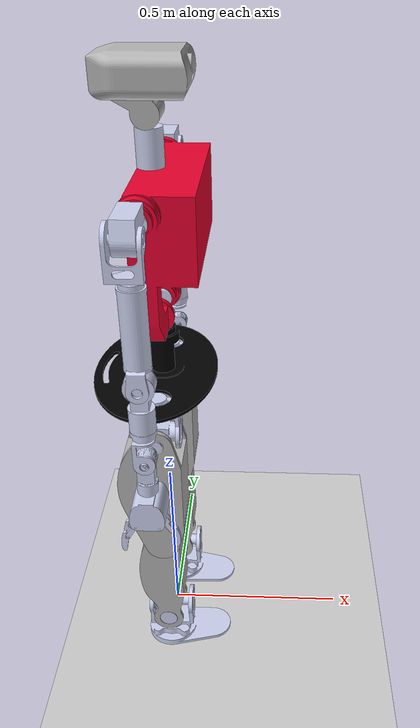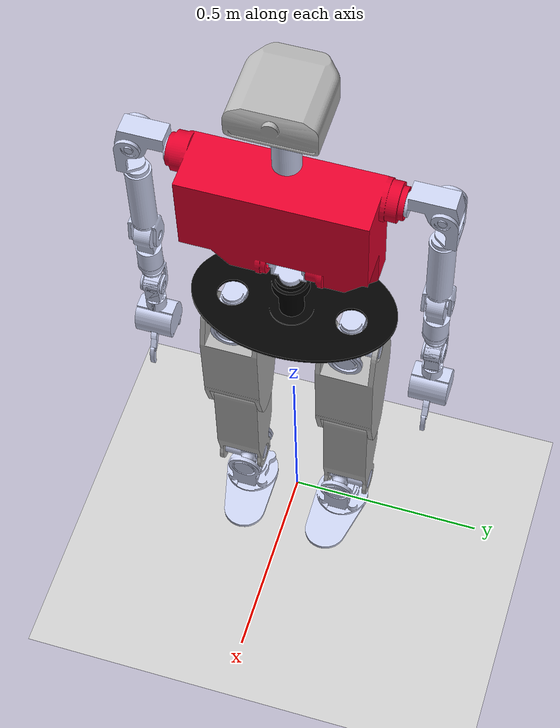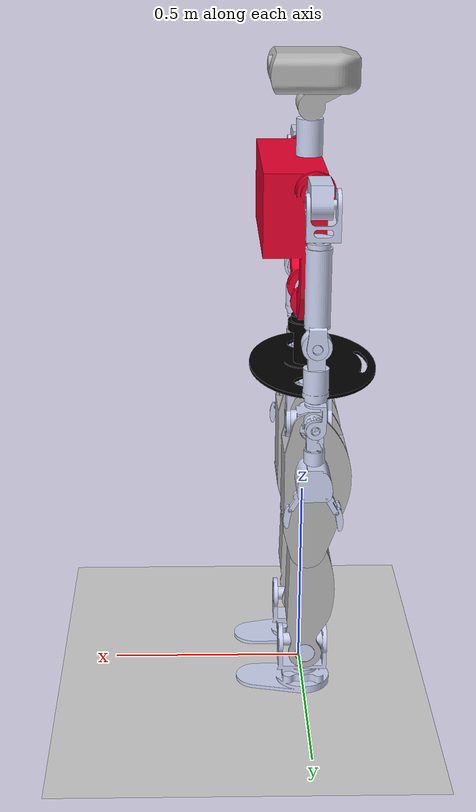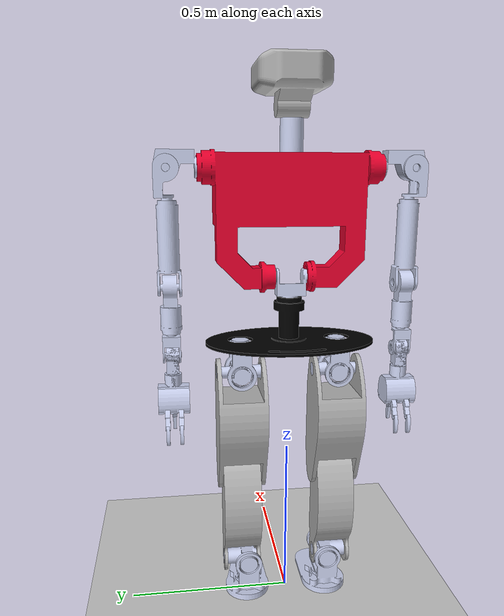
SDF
<?xml version="1.0"?>
<sdf version="1.7">
  <world name="default">

    <include>
      <uri>https://fuel.gazebosim.org/1.0/OpenRobotics/models/Sun</uri>
    </include>

    <include>
      <uri>https://fuel.gazebosim.org/1.0/OpenRobotics/models/Ground Plane</uri>
    </include>

    <include>
      <uri>model://teo_lacqueyFetch</uri>
    </include>

  </world>
</sdf>

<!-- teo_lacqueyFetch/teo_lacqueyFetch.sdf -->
<sdf version="1.7">
  <model name="TEO_lacqueyFetch">

    <include merge="true">
      <uri>model://teo</uri>
    </include>

    <include merge="true">
      <pose>0 -0.34692 0.8122 0 -0 0</pose>
      <uri>model://teo_lacqueyFetch/parts/rightLacqueyFetch.sdf</uri>
    </include>

    <joint name="RightWrist" type="fixed">
      <parent>RightSensorPlate_link</parent>
      <child>RightWrist_link</child>
    </joint>

    <include merge="true">
      <pose>0 0.34692 0.8122 0 -0 0</pose>
      <uri>model://teo_lacqueyFetch/parts/leftLacqueyFetch.sdf</uri>
    </include>

    <joint name="LeftWrist" type="fixed">
      <parent>LeftSensorPlate_link</parent>
      <child>LeftWrist_link</child>
    </joint>

    <plugin name="gzyarp::RobotInterface" filename="gz-sim-yarp-robotinterface-system">
      <yarpRobotInterfaceConfigurationFile>model://teo_lacqueyFetch/conf/teo_lacqueyFetch_nws_yarp.xml</yarpRobotInterfaceConfigurationFile>
    </plugin>

  </model>
</sdf>

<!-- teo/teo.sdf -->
<sdf version="1.7">
  <model name="TEO">

    <pose>0 0 0.845 0 -0 0</pose>

    <!-- ROOT -->

    <include merge="true">
      <uri>model://teo/parts/root.sdf</uri>
    </include>

    <joint name="AxialTrunk_adapter" type="fixed">
      <parent>RootWaist_links</parent>
      <child>AxialTrunk_link_adapter</child>
    </joint>

    <!-- TRUNK -->

    <include merge="true">
      <pose>0 0 0.1932 0 -0 0</pose>
      <uri>model://teo/parts/trunk.sdf</uri>
    </include>

    <!-- HEAD -->

    <include merge="true">
      <pose>0 0 0.6282 0 -0 0</pose>
      <uri>model://teo/parts/head.sdf</uri>
    </include>

    <joint name="AxialNeck_adapter" type="fixed">
      <parent>FrontalTrunk_link</parent>
      <child>AxialNeck_link_adapter</child>
    </joint>

    <!-- RIGHT ARM -->

    <include merge="true">
      <pose>0 -0.26292 0.4982 0 -0 0</pose>
      <uri>model://teo/parts/rightArm.sdf</uri>
    </include>

    <joint name="FrontalRightShoulder_adapter" type="fixed">
      <parent>FrontalTrunk_link</parent>
      <child>FrontalRightShoulder_link_adapter</child>
    </joint>

    <!-- LEFT ARM -->

    <include merge="true">
      <pose>0 0.26292 0.4982 0 -0 0</pose>
      <uri>model://teo/parts/leftArm.sdf</uri>
    </include>

    <joint name="FrontalLeftShoulder_adapter" type="fixed">
      <parent>FrontalTrunk_link</parent>
      <child>FrontalLeftShoulder_link_adapter</child>
    </joint>

    <!-- RIGHT LEG -->

    <include merge="true">
      <pose>0 -0.146 0 0 -0 0</pose>
      <uri>model://teo/parts/rightLeg.sdf</uri>
    </include>

    <joint name="AxialRightHip_adapter" type="fixed">
      <parent>RootWaist_links</parent>
      <child>AxialRightHip_link_adapter</child>
    </joint>

    <!-- LEFT LEG -->

    <include merge="true">
      <pose>0 0.146 0 0 -0 0</pose>
      <uri>model://teo/parts/leftLeg.sdf</uri>
    </include>

    <joint name="AxialLeftHip_adapter" type="fixed">
      <parent>RootWaist_links</parent>
      <child>AxialLeftHip_link_adapter</child>
    </joint>

    <plugin name="gz::sim::systems::SceneBroadcaster" filename="gz-sim-scene-broadcaster-system" />
    <plugin name="gz::sim::systems::Sensors" filename="gz-sim-sensors-system" />
    <plugin name="gz::sim::systems::ForceTorque" filename="gz-sim-forcetorque-system" />
    <plugin name="gz::sim::systems::Imu" filename="gz-sim-imu-system" />

    <plugin name="gzyarp::RobotInterface" filename="gz-sim-yarp-robotinterface-system">
      <yarpRobotInterfaceConfigurationFile>model://teo/conf/teo_nws_yarp.xml</yarpRobotInterfaceConfigurationFile>
    </plugin>

    <plugin name="gzyarp::RobotInterface" filename="gz-sim-yarp-robotinterface-system">
      <yarpRobotInterfaceConfigurationFile>model://teo/conf/teo_nws_ros2.xml</yarpRobotInterfaceConfigurationFile>
    </plugin>

  </model>
</sdf>

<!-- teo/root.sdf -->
<sdf version='1.7'>
<model name='TEO_root'>
  <link name='RootWaist_links'>
    <pose>0 0 0 0 -0 0</pose>
    <inertial>
      <pose>-0.010985 -0.000323 0.033148 0 -0 0</pose>
      <mass>2.5</mass>
      <inertia>
        <ixx>0.038530767</ixx>
        <ixy>-0.000000135</ixy>
        <ixz>0.000238121</ixz>
        <iyy>0.017354343</iyy>
        <iyz>-4.8e-10</iyz>
        <izz>0.053231634</izz>
      </inertia>
    </inertial>
    <visual name='RootWaist_links_visual'>
      <geometry>
        <mesh>
          <uri>model://teo/meshes/visual/RootWaist_links.dae</uri>
        </mesh>
      </geometry>
      <material>
        <ambient>0 0 0 1</ambient>
        <diffuse>0 0 0 1</diffuse>
        <specular>0 0 0 1</specular>
      </material>
    </visual>
    <collision name='RootWaist_links_collision'>
      <geometry>
        <mesh>
          <uri>model://teo/meshes/collision/RootWaist_links.stl</uri>
        </mesh>
      </geometry>
    </collision>
  </link>
</model>
</sdf>

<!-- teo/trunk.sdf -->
<sdf version="1.7">
  <model name="TEO">

    <link name="AxialTrunk_link_adapter"/>

    <link name="AxialTrunk_link">
      <pose>0 0 0 0 -0 0</pose>
      <inertial>
        <pose>-0.002235 -0.000979 -0.018814 0 -0 0</pose>
        <mass>1</mass>
        <inertia>
          <ixx>0.001977587</ixx>
          <ixy>0.00000206</ixy>
          <ixz>0.0000297</ixz>
          <iyy>0.000899729</iyy>
          <iyz>-0.00000307</iyz>
          <izz>0.001471749</izz>
        </inertia>
      </inertial>
      <visual name="AxialTrunk_visual">
        <geometry>
          <mesh>
            <uri>model://teo/meshes/visual/AxialWaist.dae</uri>
          </mesh>
        </geometry>
        <material>
          <ambient>0.792157 0.819608 0.933333 1</ambient>
          <diffuse>0.792157 0.819608 0.933333 1</diffuse>
          <specular>0.633726 0.655686 0.746667 1</specular>
        </material>
      </visual>
      <collision name="AxialTrunk_collision">
        <geometry>
          <mesh>
            <uri>model://teo/meshes/collision/AxialWaist.stl</uri>
          </mesh>
        </geometry>
      </collision>
    </link>

    <joint name="AxialTrunk" type="revolute">
      <parent>AxialTrunk_link_adapter</parent>
      <child>AxialTrunk_link</child>
      <axis>
        <xyz>0 0 1</xyz>
        <limit>
          <lower>-1.03</lower>
          <upper>0.81</upper>
        </limit>
        <dynamics>
          <damping>0.001</damping>
          <friction>0.7</friction>
        </dynamics>
      </axis>
    </joint>

    <link name="FrontalTrunk_link">
      <pose>0 0 0 0 -0 0</pose>
      <inertial>
        <pose>0.032985 -0.007876 0.220667 0 -0 0</pose>
        <mass>14.23545</mass>
        <inertia>
          <ixx>0.33566514</ixx>
          <ixy>0.000162127</ixy>
          <ixz>0.011858221</ixz>
          <iyy>0.126531585</iyy>
          <iyz>0.000914091</iyz>
          <izz>0.263359225</izz>
        </inertia>
      </inertial>
      <visual name="FrontalTrunk_visual">
        <geometry>
          <mesh>
            <uri>model://teo/meshes/visual/RootWaist.dae</uri>
          </mesh>
        </geometry>
        <material>
          <ambient>0.905882 0 0.172549 1</ambient>
          <diffuse>0.905882 0 0.172549 1</diffuse>
          <specular>0.452941 0 0.086275 1</specular>
        </material>
      </visual>
      <collision name="FrontalTrunk_collision">
        <geometry>
          <mesh>
            <uri>model://teo/meshes/collision/RootWaist.stl</uri>
          </mesh>
        </geometry>
      </collision>
      <sensor name="waist_imu" type="imu">
        <pose>0 0 0.05 0 3.14159 0</pose>
        <always_on>true</always_on>
        <update_rate>200</update_rate>
      </sensor>
    </link>

    <joint name="FrontalTrunk" type="revolute">
      <parent>AxialTrunk_link</parent>
      <child>FrontalTrunk_link</child>
      <axis>
        <xyz>0 1 0</xyz>
        <limit>
          <lower>-0.18</lower>
          <upper>1.58</upper>
        </limit>
        <dynamics>
          <damping>0.001</damping>
          <friction>0.7</friction>
        </dynamics>
      </axis>
    </joint>

    <plugin name="gzyarp::ControlBoard" filename="gz-sim-yarp-controlboard-system">
      <yarpConfigurationFile>model://teo/conf/gazebo_teo_trunk.ini</yarpConfigurationFile>
    </plugin>

    <plugin name="gzyarp::Imu" filename="gz-sim-yarp-imu-system">
      <yarpConfigurationFile>model://teo/conf/gazebo_teo_imu.ini</yarpConfigurationFile>
    </plugin>

  </model>
</sdf>

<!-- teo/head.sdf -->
<sdf version="1.7">
  <model name="TEO_head">

    <link name="AxialNeck_link_adapter"/>

    <link name="AxialNeck_link">
      <pose>0 0 0 0 -0 0</pose>
      <inertial>
        <pose>0.000302 0.000193 -0.0452 0 -0 0</pose>
        <mass>1</mass>
        <inertia>
          <ixx>0.000939063</ixx>
          <ixy>0</ixy>
          <ixz>0</ixz>
          <iyy>0.000939063</iyy>
          <iyz>0</iyz>
          <izz>0.000528125</izz>
        </inertia>
      </inertial>
      <visual name="AxialNeck_visual">
        <geometry>
          <mesh>
            <uri>model://teo/meshes/visual/AxialNeck.dae</uri>
          </mesh>
        </geometry>
        <material>
          <ambient>0.792157 0.819608 0.933333 1</ambient>
          <diffuse>0.792157 0.819608 0.933333 1</diffuse>
          <specular>0.633726 0.65568602 0.74666703 1</specular>
        </material>
      </visual>
      <collision name="AxialNeck_collision">
        <geometry>
          <mesh>
            <uri>model://teo/meshes/collision/AxialNeck.stl</uri>
          </mesh>
        </geometry>
      </collision>
    </link>

    <joint name="AxialNeck" type="revolute">
      <parent>AxialNeck_link_adapter</parent>
      <child>AxialNeck_link</child>
      <axis>
        <xyz>0 0 1</xyz>
        <limit>
          <lower>-1.22</lower>
          <upper>1.22</upper>
        </limit>
        <dynamics>
          <damping>0.001</damping>
          <friction>0.7</friction>
        </dynamics>
      </axis>
    </joint>

    <link name="FrontalNeck_link">
      <pose>0 0 0.0325 0 -0 0</pose>
      <inertial>
        <pose>-0.002729 -0.000086 0.067027 0 -0 0</pose>
        <mass>2</mass>
        <inertia>
          <ixx>0.007599322</ixx>
          <ixy>5.83e-09</ixy>
          <ixz>0.0000658</ixz>
          <iyy>0.008325273</iyy>
          <iyz>-7.43e-09</iyz>
          <izz>0.011403464</izz>
        </inertia>
      </inertial>
      <visual name="FrontalNeck_visual">
        <geometry>
          <mesh>
            <uri>model://teo/meshes/visual/FrontalNeck.dae</uri>
          </mesh>
        </geometry>
        <material>
          <ambient>1 1 1 1</ambient>
          <diffuse>0.7 0.7 0.7 1</diffuse>
          <specular>0.2 0.2 0.2 1</specular>
        </material>
      </visual>
      <collision name="FrontalNeck_collision">
        <geometry>
          <mesh>
            <uri>model://teo/meshes/collision/FrontalNeck.stl</uri>
          </mesh>
        </geometry>
      </collision>
      <sensor name="xtion_rgbd" type="rgbd_camera">
        <pose>0 0 0 0 -0 0</pose>
        <camera>
          <horizontal_fov>1.01</horizontal_fov>
          <image>
            <width>640</width>
            <height>480</height>
          </image>
          <clip>
            <near>0.2</near>
            <far>3.5</far>
          </clip>
          <lens>
            <intrinsics>
              <fx>525</fx>
              <fy>525</fy>
              <cx>319.5</cx>
              <cy>239.5</cy>
            </intrinsics>
          </lens>
        </camera>
        <always_on>1</always_on>
        <update_rate>30</update_rate>
        <visualize>1</visualize>
      </sensor>
    </link>

    <joint name="FrontalNeck" type="revolute">
      <parent>AxialNeck_link</parent>
      <child>FrontalNeck_link</child>
      <axis>
        <xyz>0 1 0</xyz>
        <limit>
          <lower>-0.51</lower>
          <upper>0.15</upper>
        </limit>
        <dynamics>
          <damping>0.001</damping>
          <friction>0.7</friction>
        </dynamics>
      </axis>
    </joint>

    <plugin name="gzyarp::ControlBoard" filename="gz-sim-yarp-controlboard-system">
      <yarpConfigurationFile>model://teo/conf/gazebo_teo_head.ini</yarpConfigurationFile>
    </plugin>

    <plugin name="gzyarp::DepthCamera" filename="gz-sim-yarp-depthcamera-system">
      <yarpConfigurationFile>model://teo/conf/gazebo_teo_rgbd.ini</yarpConfigurationFile>
    </plugin>

  </model>
</sdf>

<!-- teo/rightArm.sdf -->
<sdf version="1.7">
  <model name="TEO_rightArm">

    <link name="FrontalRightShoulder_link_adapter"/>

    <link name="FrontalRightShoulder_link">
      <pose>0 0 0 0 -0 0</pose>
      <inertial>
        <pose>-0.002267 -0.056164 0.008456 0 -0 0</pose>
        <mass>2</mass>
        <inertia>
          <ixx>0.004226791</ixx>
          <ixy>0.0000844</ixy>
          <ixz>-0.0000117</ixz>
          <iyy>0.002127281</iyy>
          <iyz>-0.000280493</iyz>
          <izz>0.004093161</izz>
        </inertia>
      </inertial>
      <visual name="FrontalRightShoulder_visual">
        <geometry>
          <mesh>
            <uri>model://teo/meshes/visual/FrontalRightShoulder.dae</uri>
          </mesh>
        </geometry>
        <material>
          <ambient>0.792157 0.819608 0.933333 1</ambient>
          <diffuse>0.792157 0.819608 0.933333 1</diffuse>
          <specular>0.633726 0.655686 0.746667 1</specular>
        </material>
      </visual>
      <collision name="FrontalRightShoulder_collision">
        <geometry>
          <mesh>
            <uri>model://teo/meshes/collision/FrontalRightShoulder.stl</uri>
          </mesh>
        </geometry>
      </collision>
    </link>

    <joint name="FrontalRightShoulder" type="revolute">
      <parent>FrontalRightShoulder_link_adapter</parent>
      <child>FrontalRightShoulder_link</child>
      <axis>
        <xyz>0 1 0</xyz>
        <limit>
          <lower>-1.71</lower>
          <upper>1.85</upper>
        </limit>
        <dynamics>
          <damping>0.001</damping>
          <friction>0.7</friction>
        </dynamics>
      </axis>
    </joint>

    <link name="SagittalRightShoulder_link">
      <pose>0 -0.084 0 0 -0 0</pose>
      <inertial>
        <pose>-0.008472 -0.004826 -0.027321 0 -0 0</pose>
        <mass>1</mass>
        <inertia>
          <ixx>0.001610932</ixx>
          <ixy>-0.000069</ixy>
          <ixz>-0.000214886</ixz>
          <iyy>0.002187776</iyy>
          <iyz>-0.000069</iyz>
          <izz>0.001173533</izz>
        </inertia>
      </inertial>
      <visual name="SagittalRightShoulder_visual">
        <geometry>
          <mesh>
            <uri>model://teo/meshes/visual/SagittalRightShoulder.dae</uri>
          </mesh>
        </geometry>
        <material>
          <ambient>0.792157 0.819608 0.933333 1</ambient>
          <diffuse>0.792157 0.819608 0.933333 1</diffuse>
          <specular>0.633726 0.655686 0.746667 1</specular>
        </material>
      </visual>
      <collision name="SagittalRightShoulder_collision">
        <geometry>
          <mesh>
            <uri>model://teo/meshes/collision/SagittalRightShoulder.stl</uri>
          </mesh>
        </geometry>
      </collision>
    </link>

    <joint name="SagittalRightShoulder" type="revolute">
      <parent>FrontalRightShoulder_link</parent>
      <child>SagittalRightShoulder_link</child>
      <axis>
        <xyz>1 0 0</xyz>
        <limit>
          <lower>-1.32</lower>
          <upper>0.39</upper>
        </limit>
        <dynamics>
          <damping>0.001</damping>
          <friction>0.7</friction>
        </dynamics>
      </axis>
    </joint>

    <link name="AxialRightShoulder_link">
      <pose>0 -0.084 -0.329 0 -0 0</pose>
      <inertial>
        <pose>0.000347 0.000245 0.107382 0 -0 0</pose>
        <mass>1</mass>
      </inertial>
      <visual name="AxialRightShoulder_visual">
        <geometry>
          <mesh>
            <uri>model://teo/meshes/visual/AxialRightShoulder.dae</uri>
          </mesh>
        </geometry>
        <material>
          <ambient>0.792157 0.819608 0.933333 1</ambient>
          <diffuse>0.792157 0.819608 0.933333 1</diffuse>
          <specular>0.633726 0.655686 0.746667 1</specular>
        </material>
      </visual>
      <collision name="AxialRightShoulder_collision">
        <geometry>
          <mesh>
            <uri>model://teo/meshes/collision/AxialRightShoulder.stl</uri>
          </mesh>
        </geometry>
      </collision>
    </link>

    <joint name="AxialRightShoulder" type="revolute">
      <parent>SagittalRightShoulder_link</parent>
      <child>AxialRightShoulder_link</child>
      <axis>
        <xyz>0 0 1</xyz>
        <limit>
          <lower>-1.4</lower>
          <upper>0.99</upper>
        </limit>
        <dynamics>
          <damping>0.001</damping>
          <friction>0.7</friction>
        </dynamics>
      </axis>
    </joint>

    <link name="FrontalRightElbow_link">
      <pose>0 -0.084 -0.329 0 -0 0</pose>
      <inertial>
        <pose>0.000237 -0.00004 -0.04998 0 -0 0</pose>
        <mass>1</mass>
        <inertia>
          <ixx>0.002590029</ixx>
          <ixy>0</ixy>
          <ixz>0</ixz>
          <iyy>0.00262307</iyy>
          <iyz>0</iyz>
          <izz>0.000446024</izz>
        </inertia>
      </inertial>
      <visual name="FrontalRightElbow_visual">
        <geometry>
          <mesh>
            <uri>model://teo/meshes/visual/FrontalRightElbow.dae</uri>
          </mesh>
        </geometry>
        <material>
          <ambient>0.792157 0.819608 0.933333 1</ambient>
          <diffuse>0.792157 0.819608 0.933333 1</diffuse>
          <specular>0.633726 0.655686 0.746667 1</specular>
        </material>
      </visual>
      <collision name="FrontalRightElbow_collision">
        <geometry>
          <mesh>
            <uri>model://teo/meshes/collision/FrontalRightElbow.stl</uri>
          </mesh>
        </geometry>
      </collision>
    </link>

    <joint name="FrontalRightElbow" type="revolute">
      <parent>AxialRightShoulder_link</parent>
      <child>FrontalRightElbow_link</child>
      <axis>
        <xyz>0 1 0</xyz>
        <limit>
          <lower>-1.74</lower>
          <upper>1.72</upper>
        </limit>
        <dynamics>
          <damping>0.001</damping>
          <friction>0.7</friction>
        </dynamics>
      </axis>
    </joint>

    <link name="AxialRightWrist_link">
      <pose>0 -0.084 -0.531 0 -0 0</pose>
      <inertial>
        <pose>-0.001151 0.000603 0.02464 0 -0 0</pose>
        <mass>0.63149</mass>
      </inertial>
      <visual name="AxialRightWrist_visual">
        <geometry>
          <mesh>
            <uri>model://teo/meshes/visual/AxialRightWrist.dae</uri>
          </mesh>
        </geometry>
        <material>
          <ambient>0.792157 0.819608 0.933333 1</ambient>
          <diffuse>0.792157 0.819608 0.933333 1</diffuse>
          <specular>0.633726 0.655686 0.746667 1</specular>
        </material>
      </visual>
      <collision name="AxialRightWrist_collision">
        <geometry>
          <mesh>
            <uri>model://teo/meshes/collision/AxialRightWrist.stl</uri>
          </mesh>
        </geometry>
      </collision>
    </link>

    <joint name="AxialRightWrist" type="revolute">
      <parent>FrontalRightElbow_link</parent>
      <child>AxialRightWrist_link</child>
      <axis>
        <xyz>0 0 1</xyz>
        <limit>
          <lower>-1.4</lower>
          <upper>1.74</upper>
        </limit>
        <dynamics>
          <damping>0.001</damping>
          <friction>0.7</friction>
        </dynamics>
      </axis>
    </joint>

    <link name="FrontalRightWrist_link">
      <pose>0 -0.084 -0.531 0 -0 0</pose>
      <inertial>
        <pose>-0.002314 0.00007 -0.108635 0 -0 0</pose>
        <mass>0.72</mass>
        <inertia>
          <ixx>0.005329957</ixx>
          <ixy>0.000000102</ixy>
          <ixz>0.000114751</ixz>
          <iyy>0.005345282</iyy>
          <iyz>-0.00000807</iyz>
          <izz>0.000883179</izz>
        </inertia>
      </inertial>
      <visual name="FrontalRightWrist_visual">
        <pose>0 0 0 -1.5708 0 0</pose>
        <geometry>
          <mesh>
            <scale>0.001 0.001 0.001</scale>
            <uri>model://teo/meshes/visual/FrontalRightWrist.dae</uri>
          </mesh>
        </geometry>
        <material>
          <ambient>0.792157 0.819608 0.933333 1</ambient>
          <diffuse>0.792157 0.819608 0.933333 1</diffuse>
          <specular>0.633726 0.655686 0.746667 1</specular>
        </material>
      </visual>
      <collision name="FrontalRightWrist_collision">
        <pose>0 0 0 -1.5708 0 0</pose>
        <geometry>
          <mesh>
            <scale>0.001 0.001 0.001</scale>
            <uri>model://teo/meshes/collision/FrontalRightWrist.stl</uri>
          </mesh>
        </geometry>
      </collision>
    </link>

    <joint name="FrontalRightWrist" type="revolute">
      <parent>AxialRightWrist_link</parent>
      <child>FrontalRightWrist_link</child>
      <axis>
        <xyz>0 1 0</xyz>
        <limit>
          <lower>-2.01</lower>
          <upper>0.78</upper>
        </limit>
        <dynamics>
          <damping>0.001</damping>
          <friction>0.7</friction>
        </dynamics>
      </axis>
    </joint>

    <link name="RightSensorPlate_link">
      <pose>0 -0.084 -0.63401 0 -0 0</pose>
      <inertial>
        <mass>0.001</mass> <!-- can"t be zero! -->
      </inertial>
    </link>

    <joint name="RightSensorPlate" type="fixed">
      <parent>FrontalRightWrist_link</parent>
      <child>RightSensorPlate_link</child>
      <pose>0 0 0 0 3.141593 0</pose>
      <sensor name="rightArm_ft" type="force_torque">
        <always_on>true</always_on>
        <update_rate>200</update_rate>
        <force_torque>
          <frame>sensor</frame>
          <measure_direction>child_to_parent</measure_direction>
        </force_torque>
      </sensor>
    </joint>

    <plugin name="gzyarp::ControlBoard" filename="gz-sim-yarp-controlboard-system">
      <yarpConfigurationFile>model://teo/conf/gazebo_teo_rightArm.ini</yarpConfigurationFile>
    </plugin>

    <plugin name="gzyarp::ForceTorque" filename="gz-sim-yarp-forcetorque-system">
      <yarpConfigurationFile>model://teo/conf/gazebo_teo_rightArm_ft.ini</yarpConfigurationFile>
    </plugin>

  </model>
</sdf>

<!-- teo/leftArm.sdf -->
<sdf version="1.7">
  <model name="TEO_leftArm">

    <link name="FrontalLeftShoulder_link_adapter"/>

    <link name="FrontalLeftShoulder_link">
      <pose>0 0 0 0 -0 0</pose>
      <inertial>
        <pose>-0.002272 0.056186 0.008165 0 -0 0</pose>
        <mass>2</mass>
        <inertia>
          <ixx>0.004226791</ixx>
          <ixy>-0.0000855</ixy>
          <ixz>-0.0000117</ixz>
          <iyy>0.00212734</iyy>
          <iyz>0.000280493</iyz>
          <izz>0.00409322</izz>
        </inertia>
      </inertial>
      <visual name="FrontalLeftShoulder_visual">
        <geometry>
          <mesh>
            <uri>model://teo/meshes/visual/FrontalLeftShoulder.dae</uri>
          </mesh>
        </geometry>
        <material>
          <ambient>0.792157 0.819608 0.933333 1</ambient>
          <diffuse>0.792157 0.819608 0.933333 1</diffuse>
          <specular>0.633726 0.655686 0.746667 1</specular>
        </material>
      </visual>
      <collision name="FrontalLeftShoulder_collision">
        <geometry>
          <mesh>
            <uri>model://teo/meshes/collision/FrontalLeftShoulder.stl</uri>
          </mesh>
        </geometry>
      </collision>
    </link>

    <joint name="FrontalLeftShoulder" type="revolute">
      <parent>FrontalLeftShoulder_link_adapter</parent>
      <child>FrontalLeftShoulder_link</child>
      <axis>
        <xyz>0 1 0</xyz>
        <limit>
          <lower>-1.69</lower>
          <upper>1.98</upper>
        </limit>
        <dynamics>
          <damping>0.001</damping>
          <friction>0.7</friction>
        </dynamics>
      </axis>
    </joint>

    <link name="SagittalLeftShoulder_link">
      <pose>0 0.084 0 0 -0 0</pose>
      <inertial>
        <pose>-0.008047 0.004937 -0.027619 0 -0 0</pose>
        <mass>1</mass>
        <inertia>
          <ixx>0.001610921</ixx>
          <ixy>0.000069</ixy>
          <ixz>-0.000214885</ixz>
          <iyy>0.002187768</iyy>
          <iyz>-0.000163004</iyz>
          <izz>0.001173531</izz>
        </inertia>
      </inertial>
      <visual name="SagittalLeftShoulder_visual">
        <geometry>
          <mesh>
            <uri>model://teo/meshes/visual/SagittalLeftShoulder.dae</uri>
          </mesh>
        </geometry>
        <material>
          <ambient>0.792157 0.819608 0.933333 1</ambient>
          <diffuse>0.792157 0.819608 0.933333 1</diffuse>
          <specular>0.633726 0.655686 0.746667 1</specular>
        </material>
      </visual>
      <collision name="SagittalLeftShoulder_collision">
        <geometry>
          <mesh>
            <uri>model://teo/meshes/collision/SagittalLeftShoulder.stl</uri>
          </mesh>
        </geometry>
      </collision>
    </link>

    <joint name="SagittalLeftShoulder" type="revolute">
      <parent>FrontalLeftShoulder_link</parent>
      <child>SagittalLeftShoulder_link</child>
      <axis>
        <xyz>1 0 0</xyz>
        <limit>
          <lower>-0.42</lower>
          <upper>1.34</upper>
        </limit>
        <dynamics>
          <damping>0.001</damping>
          <friction>0.7</friction>
        </dynamics>
      </axis>
    </joint>

    <link name="AxialLeftShoulder_link">
      <pose>0 0.084 -0.329 0 -0 0</pose>
      <inertial>
        <pose>-0.000172 0.000249 0.100649 0 -0 0</pose>
      </inertial>
      <visual name="AxialLeftShoulder_visual">
        <geometry>
          <mesh>
            <uri>model://teo/meshes/visual/AxialLeftShoulder.dae</uri>
          </mesh>
        </geometry>
        <material>
          <ambient>0.792157 0.819608 0.933333 1</ambient>
          <diffuse>0.792157 0.819608 0.933333 1</diffuse>
          <specular>0.633726 0.655686 0.746667 1</specular>
        </material>
      </visual>
      <collision name="AxialLeftShoulder_collision">
        <geometry>
          <mesh>
            <uri>model://teo/meshes/collision/AxialLeftShoulder.stl</uri>
          </mesh>
        </geometry>
      </collision>
    </link>

    <joint name="AxialLeftShoulder" type="revolute">
      <parent>SagittalLeftShoulder_link</parent>
      <child>AxialLeftShoulder_link</child>
      <axis>
        <xyz>0 0 1</xyz>
        <limit>
          <lower>-0.9</lower>
          <upper>1.47</upper>
        </limit>
        <dynamics>
          <damping>0.001</damping>
          <friction>0.7</friction>
        </dynamics>
      </axis>
    </joint>

    <link name="FrontalLeftElbow_link">
      <pose>0 0.084 -0.329 0 -0 0</pose>
      <inertial>
        <pose>0.000287 -0.000116 -0.053185 0 -0 0</pose>
        <mass>1</mass>
        <inertia>
          <ixx>0.002590029</ixx>
          <ixy>0</ixy>
          <ixz>0</ixz>
          <iyy>0.00262307</iyy>
          <iyz>0</iyz>
          <izz>0.000446024</izz>
        </inertia>
      </inertial>
      <visual name="FrontalLeftElbow_visual">
        <geometry>
          <mesh>
            <uri>model://teo/meshes/visual/FrontalLeftElbow.dae</uri>
          </mesh>
        </geometry>
        <material>
          <ambient>0.792157 0.819608 0.933333 1</ambient>
          <diffuse>0.792157 0.819608 0.933333 1</diffuse>
          <specular>0.633726 0.655686 0.746667 1</specular>
        </material>
      </visual>
      <collision name="FrontalLeftElbow_collision">
        <geometry>
          <mesh>
            <uri>model://teo/meshes/collision/FrontalLeftElbow.stl</uri>
          </mesh>
        </geometry>
      </collision>
    </link>

    <joint name="FrontalLeftElbow" type="revolute">
      <parent>AxialLeftShoulder_link</parent>
      <child>FrontalLeftElbow_link</child>
      <axis>
        <xyz>0 1 0</xyz>
        <limit>
          <lower>-1.76</lower>
          <upper>1.69</upper>
        </limit>
        <dynamics>
          <damping>0.001</damping>
          <friction>0.7</friction>
        </dynamics>
      </axis>
    </joint>

    <link name="AxialLeftWrist_link">
      <pose>0 0.084 -0.531 0 -0 0</pose>
      <inertial>
        <pose>-0.001151 0.000603 0.02464 0 -0 0</pose>
        <mass>0.63149</mass>
      </inertial>
      <visual name="AxialLeftWrist_visual">
        <geometry>
          <mesh>
            <uri>model://teo/meshes/visual/AxialLeftWrist.dae</uri>
          </mesh>
        </geometry>
        <material>
          <ambient>0.792157 0.819608 0.933333 1</ambient>
          <diffuse>0.792157 0.819608 0.933333 1</diffuse>
          <specular>0.633726 0.655686 0.746667 1</specular>
        </material>
      </visual>
      <collision name="AxialLeftWrist_collision">
        <geometry>
          <mesh>
            <uri>model://teo/meshes/collision/AxialLeftWrist.stl</uri>
          </mesh>
        </geometry>
      </collision>
    </link>

    <joint name="AxialLeftWrist" type="revolute">
      <parent>FrontalLeftElbow_link</parent>
      <child>AxialLeftWrist_link</child>
      <axis>
        <xyz>0 0 1</xyz>
        <limit>
          <lower>-1.77</lower>
          <upper>1.33</upper>
        </limit>
        <dynamics>
          <damping>0.001</damping>
          <friction>0.7</friction>
        </dynamics>
      </axis>
    </joint>

    <link name="FrontalLeftWrist_link">
      <pose>0 0.084 -0.531 0 -0 0</pose>
      <inertial>
        <pose>-0.002314 0.00007 -0.108635 0 -0 0</pose>
        <mass>0.72</mass>
        <inertia>
          <ixx>0.005330647</ixx>
          <ixy>0.000000128</ixy>
          <ixz>0.000100487</ixz>
          <iyy>0.005345282</iyy>
          <iyz>-0.00000807</iyz>
          <izz>0.000882489</izz>
        </inertia>
      </inertial>
      <visual name="FrontalLeftWrist_visual">
        <pose>0 0 0 -1.5708 0 0</pose>
        <geometry>
          <mesh>
            <scale>0.001 0.001 0.001</scale>
            <uri>model://teo/meshes/visual/FrontalLeftWrist.dae</uri>
          </mesh>
        </geometry>
        <material>
          <ambient>0.792157 0.819608 0.933333 1</ambient>
          <diffuse>0.792157 0.819608 0.933333 1</diffuse>
          <specular>0.633726 0.655686 0.746667 1</specular>
        </material>
      </visual>
      <collision name="FrontalLeftWrist_collision">
        <pose>0 0 0 -1.5708 0 0</pose>
        <geometry>
          <mesh>
            <scale>0.001 0.001 0.001</scale>
            <uri>model://teo/meshes/collision/FrontalLeftWrist.stl</uri>
          </mesh>
        </geometry>
      </collision>
    </link>

    <joint name="FrontalLeftWrist" type="revolute">
      <parent>AxialLeftWrist_link</parent>
      <child>FrontalLeftWrist_link</child>
      <axis>
        <xyz>0 1 0</xyz>
        <limit>
          <lower>-1.98</lower>
          <upper>1.07</upper>
        </limit>
        <dynamics>
          <damping>0.001</damping>
          <friction>0.7</friction>
        </dynamics>
      </axis>
    </joint>

    <link name="LeftSensorPlate_link">
      <pose>0 0.084 -0.63401 0 -0 0</pose>
      <inertial>
        <mass>0.001</mass> <!-- can"t be zero! -->
      </inertial>
    </link>

    <joint name="LeftSensorPlate" type="fixed">
      <parent>FrontalLeftWrist_link</parent>
      <child>LeftSensorPlate_link</child>
      <pose>0 0 0 0 3.141593 0</pose>
      <sensor name="leftArm_ft" type="force_torque">
        <always_on>true</always_on>
        <update_rate>200</update_rate>
        <force_torque>
          <frame>sensor</frame>
          <measure_direction>child_to_parent</measure_direction>
        </force_torque>
      </sensor>
    </joint>

    <plugin name="gzyarp::ControlBoard" filename="gz-sim-yarp-controlboard-system">
      <yarpConfigurationFile>model://teo/conf/gazebo_teo_leftArm.ini</yarpConfigurationFile>
    </plugin>

    <plugin name="gzyarp::ForceTorque" filename="gz-sim-yarp-forcetorque-system">
      <yarpConfigurationFile>model://teo/conf/gazebo_teo_leftArm_ft.ini</yarpConfigurationFile>
    </plugin>

  </model>
</sdf>

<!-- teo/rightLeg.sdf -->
<sdf version="1.7">
  <model name="TEO_rightLeg">

    <link name="AxialRightHip_link_adapter"/>

    <link name="AxialRightHip_link">
      <pose>0 0 0 0 -0 0</pose>
      <inertial>
        <pose>0.000089 -0.000389 -0.065985 0 -0 0</pose>
        <mass>0.84945</mass>
        <inertia>
          <ixx>0.001564202</ixx>
          <ixy>0</ixy>
          <ixz>0.0000025</ixz>
          <iyy>0.002645089</iyy>
          <iyz>0</iyz>
          <izz>0.001706349</izz>
        </inertia>
      </inertial>
      <visual name="AxialRightHip_visual">
        <geometry>
          <mesh>
            <uri>model://teo/meshes/visual/AxialRightHip.dae</uri>
          </mesh>
        </geometry>
        <material>
          <ambient>0.792157 0.819608 0.933333 1</ambient>
          <diffuse>0.792157 0.819608 0.933333 1</diffuse>
          <specular>0.633726 0.655686 0.746667 1</specular>
        </material>
      </visual>
      <collision name="AxialRightHip_collision">
        <geometry>
          <mesh>
            <uri>model://teo/meshes/collision/AxialRightHip.stl</uri>
          </mesh>
        </geometry>
      </collision>
    </link>

    <joint name="AxialRightHip" type="revolute">
      <parent>AxialRightHip_link_adapter</parent>
      <child>AxialRightHip_link</child>
      <axis>
        <xyz>0 0 1</xyz>
        <limit>
          <lower>-0.57</lower>
          <upper>0.49</upper>
        </limit>
        <dynamics>
          <damping>0.001</damping>
          <friction>0.7</friction>
        </dynamics>
      </axis>
    </joint>

    <link name="SagittalRightHip_link">
      <pose>0 0 -0.092 0 -0 0</pose>
      <inertial>
        <pose>-0.000636 0.001058 0.000349 0 -0 0</pose>
        <mass>1.45459</mass>
        <inertia>
          <ixx>0.001545815</ixx>
          <ixy>-0.00000297</ixy>
          <ixz>-4.07e-09</ixz>
          <iyy>0.00119159</iyy>
          <iyz>9.16e-09</iyz>
          <izz>0.002270482</izz>
        </inertia>
      </inertial>
      <visual name="SagittalRightHip_visual">
        <geometry>
          <mesh>
            <uri>model://teo/meshes/visual/SagittalRightHip.dae</uri>
          </mesh>
        </geometry>
        <material>
          <ambient>0.792157 0.819608 0.933333 1</ambient>
          <diffuse>0.792157 0.819608 0.933333 1</diffuse>
          <specular>0.633726 0.655686 0.746667 1</specular>
        </material>
      </visual>
      <collision name="SagittalRightHip_collision">
        <geometry>
          <mesh>
            <uri>model://teo/meshes/collision/SagittalRightHip.stl</uri>
          </mesh>
        </geometry>
      </collision>
    </link>

    <joint name="SagittalRightHip" type="revolute">
      <parent>AxialRightHip_link</parent>
      <child>SagittalRightHip_link</child>
      <axis>
        <xyz>1 0 0</xyz>
        <limit>
          <lower>-0.25</lower>
          <upper>0.22</upper>
        </limit>
        <dynamics>
          <damping>0.001</damping>
          <friction>0.7</friction>
        </dynamics>
      </axis>
    </joint>

    <link name="FrontalRightHip_link">
      <pose>0 0 -0.092 0 -0 0</pose>
      <inertial>
        <pose>-0.010862 -0.000006 -0.161205 0 -0 0</pose>
        <mass>1.89152</mass>
        <inertia>
          <ixx>0.015077735</ixx>
          <ixy>0</ixy>
          <ixz>-0.000442074</ixz>
          <iyy>0.015112044</iyy>
          <iyz>0</iyz>
          <izz>0.00747346</izz>
        </inertia>
      </inertial>
      <visual name="FrontalRightHip_visual">
        <geometry>
          <mesh>
            <uri>model://teo/meshes/visual/FrontalRightHip.dae</uri>
          </mesh>
        </geometry>
        <material>
          <ambient>1 1 1 1</ambient>
          <diffuse>0.7 0.7 0.7 1</diffuse>
          <specular>0.2 0.2 0.2 1</specular>
        </material>
      </visual>
      <collision name="FrontalRightHip_collision">
        <geometry>
          <mesh>
            <uri>model://teo/meshes/collision/FrontalRightHip.stl</uri>
          </mesh>
        </geometry>
      </collision>
    </link>

    <joint name="FrontalRightHip" type="revolute">
      <parent>SagittalRightHip_link</parent>
      <child>FrontalRightHip_link</child>
      <axis>
        <xyz>0 1 0</xyz>
        <limit>
          <lower>-0.55</lower>
          <upper>0.74</upper>
        </limit>
        <dynamics>
          <damping>0.001</damping>
          <friction>0.7</friction>
        </dynamics>
      </axis>
    </joint>

    <link name="FrontalRightKnee_link">
      <pose>0 0 -0.422 0 -0 0</pose>
      <inertial>
        <pose>-0.006614 -0.000411 -0.146413 0 -0 0</pose>
        <mass>1.94824</mass>
        <inertia>
          <ixx>0.02186171</ixx>
          <ixy>0</ixy>
          <ixz>0.00000316</ixz>
          <iyy>0.021411109</iyy>
          <iyz>0</iyz>
          <izz>0.003843636</izz>
        </inertia>
      </inertial>
      <visual name="FrontalRightKnee_visual">
        <geometry>
          <mesh>
            <uri>model://teo/meshes/visual/FrontalRightKnee.dae</uri>
          </mesh>
        </geometry>
        <material>
          <ambient>1 1 1 1</ambient>
          <diffuse>0.7 0.7 0.7 1</diffuse>
          <specular>0.2 0.2 0.2 1</specular>
        </material>
      </visual>
      <collision name="FrontalRightKnee_collision">
        <geometry>
          <mesh>
            <uri>model://teo/meshes/collision/FrontalRightKnee.stl</uri>
          </mesh>
        </geometry>
      </collision>
    </link>

    <joint name="FrontalRightKnee" type="revolute">
      <parent>FrontalRightHip_link</parent>
      <child>FrontalRightKnee_link</child>
      <axis>
        <xyz>0 1 0</xyz>
        <limit>
          <lower>-1.07</lower>
          <upper>1.44</upper>
        </limit>
        <dynamics>
          <damping>0.001</damping>
          <friction>0.7</friction>
        </dynamics>
      </axis>
    </joint>

    <link name="FrontalRightAnkle_link">
      <pose>0 0.0175 -0.722 0 -0 0</pose>
      <inertial>
        <pose>0.002577 -0.013536 0.000182 0 -0 0</pose>
        <mass>1.50359</mass>
        <inertia>
          <ixx>0.001395488</ixx>
          <ixy>0.00000685</ixy>
          <ixz>1e-11</ixz>
          <iyy>0.001589358</iyy>
          <iyz>0</iyz>
          <izz>0.002418657</izz>
        </inertia>
      </inertial>
      <visual name="FrontalRightAnkle_visual">
        <geometry>
          <mesh>
            <uri>model://teo/meshes/visual/FrontalRightAnkle.dae</uri>
          </mesh>
        </geometry>
        <material>
          <ambient>0.792157 0.819608 0.933333 1</ambient>
          <diffuse>0.792157 0.819608 0.933333 1</diffuse>
          <specular>0.633726 0.655686 0.746667 1</specular>
        </material>
      </visual>
      <collision name="FrontalRightAnkle_collision">
        <geometry>
          <mesh>
            <uri>model://teo/meshes/collision/FrontalRightAnkle.stl</uri>
          </mesh>
        </geometry>
      </collision>
    </link>

    <joint name="FrontalRightAnkle" type="revolute">
      <parent>FrontalRightKnee_link</parent>
      <child>FrontalRightAnkle_link</child>
      <axis>
        <xyz>0 1 0</xyz>
        <limit>
          <lower>-0.4</lower>
          <upper>0.44</upper>
        </limit>
        <dynamics>
          <damping>0.001</damping>
          <friction>0.7</friction>
        </dynamics>
      </axis>
    </joint>

    <link name="SagittalRightAnkle_link">
      <pose>0 0.0175 -0.722 0 -0 0</pose>
      <inertial>
        <pose>0.01003 0.000936 -0.0669 0 -0 0</pose>
        <mass>2.1334</mass>
        <inertia>
          <ixx>0.00774203</ixx>
          <ixy>0.000455866</ixy>
          <ixz>-0.001851657</ixz>
          <iyy>0.014781323</iyy>
          <iyz>-0.000147513</iyz>
          <izz>0.013361748</izz>
        </inertia>
      </inertial>
      <visual name="FrontalRightAnkle_visual">
        <geometry>
          <mesh>
            <uri>model://teo/meshes/visual/SagittalRightAnkle.dae</uri>
          </mesh>
        </geometry>
        <material>
          <ambient>0.792157 0.819608 0.933333 1</ambient>
          <diffuse>0.792157 0.819608 0.933333 1</diffuse>
          <specular>0.633726 0.655686 0.746667 1</specular>
        </material>
      </visual>
      <collision name="SagittalRightAnkle_collision">
        <geometry>
          <mesh>
            <uri>model://teo/meshes/collision/SagittalRightAnkle.stl</uri>
          </mesh>
        </geometry>
      </collision>
    </link>

    <joint name="SagittalRightAnkle" type="revolute">
      <parent>FrontalRightAnkle_link</parent>
      <child>SagittalRightAnkle_link</child>
      <axis>
        <xyz>1 0 0</xyz>
        <limit>
          <lower>-0.35</lower>
          <upper>0.74</upper>
        </limit>
        <dynamics>
          <damping>0.001</damping>
          <friction>0.7</friction>
        </dynamics>
      </axis>
    </joint>

    <link name="SagittalRightFoot_link">
      <pose>0 0.0175 -0.722 0 -0 0</pose>
      <inertial>
        <pose>0.01003 0.000936 -0.0669 0 -0 0</pose>
        <mass>1.0</mass>
        <inertia>
          <ixx>0.00774203</ixx>
          <ixy>0.000455866</ixy>
          <ixz>-0.001851657</ixz>
          <iyy>0.014781323</iyy>
          <iyz>-0.000147513</iyz>
          <izz>0.013361748</izz>
        </inertia>
      </inertial>
      <visual name="FrontalRightFoot_visual">
        <geometry>
          <mesh>
            <uri>model://teo/meshes/visual/SagittalRightFoot.dae</uri>
          </mesh>
        </geometry>
        <material>
          <ambient>0.792157 0.819608 0.933333 1</ambient>
          <diffuse>0.792157 0.819608 0.933333 1</diffuse>
          <specular>0.633726 0.655686 0.746667 1</specular>
        </material>
      </visual>
      <collision name="SagittalRightFoot_collision">
        <geometry>
          <mesh>
            <uri>model://teo/meshes/collision/SagittalRightFoot.stl</uri>
          </mesh>
        </geometry>
        <max_contacts>4</max_contacts>
        <surface>
          <contact>
            <ode>
              <kp>18000000</kp>
              <kd>100</kd>
              <max_vel>100</max_vel>
              <min_depth>0.0001</min_depth>
            </ode>
          </contact>
          <friction>
            <ode/>
          </friction>
        </surface>
      </collision>
    </link>

    <joint name="SagittalRightFoot" type="fixed">
      <parent>SagittalRightAnkle_link</parent>
      <child>SagittalRightFoot_link</child>
      <pose>0 0 -0.113 3.141593 0 0</pose>
      <sensor name="rightLeg_ft" type="force_torque">
        <always_on>true</always_on>
        <update_rate>200</update_rate>
        <force_torque>
          <frame>sensor</frame>
          <measure_direction>child_to_parent</measure_direction>
        </force_torque>
      </sensor>
    </joint>

    <plugin name="gzyarp::ControlBoard" filename="gz-sim-yarp-controlboard-system">
      <yarpConfigurationFile>model://teo/conf/gazebo_teo_rightLeg.ini</yarpConfigurationFile>
    </plugin>

    <plugin name="gzyarp::ForceTorque" filename="gz-sim-yarp-forcetorque-system">
      <yarpConfigurationFile>model://teo/conf/gazebo_teo_rightLeg_ft.ini</yarpConfigurationFile>
    </plugin>

  </model>
</sdf>

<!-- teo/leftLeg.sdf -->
<sdf version='1.7'>
  <model name='TEO_leftLeg'>

    <link name='AxialLeftHip_link_adapter'/>

    <link name='AxialLeftHip_link'>
      <pose>0 0 0 0 -0 0</pose>
      <inertial>
        <pose>0.000089 -0.000389 -0.065985 0 -0 0</pose>
        <mass>0.84945</mass>
        <inertia>
          <ixx>0.001564202</ixx>
          <ixy>0.0000025</ixy>
          <ixz>0</ixz>
          <iyy>0.002645089</iyy>
          <iyz>0</iyz>
          <izz>0.001706349</izz>
        </inertia>
      </inertial>
      <visual name='AxialLeftHip_visual'>
        <geometry>
          <mesh>
            <uri>model://teo/meshes/visual/AxialLeftHip.dae</uri>
          </mesh>
        </geometry>
        <material>
          <ambient>0.792157 0.819608 0.933333 1</ambient>
          <diffuse>0.792157 0.819608 0.933333 1</diffuse>
          <specular>0.633726 0.655686 0.746667 1</specular>
        </material>
      </visual>
      <collision name='AxialLeftHip_collision'>
        <geometry>
          <mesh>
            <uri>model://teo/meshes/collision/AxialLeftHip.stl</uri>
          </mesh>
        </geometry>
      </collision>
    </link>

    <joint name='AxialLeftHip' type='revolute'>
      <parent>AxialLeftHip_link_adapter</parent>
      <child>AxialLeftHip_link</child>
      <axis>
        <xyz>0 0 1</xyz>
        <limit>
          <lower>-0.49</lower>
          <upper>0.57</upper>
        </limit>
        <dynamics>
          <damping>0.001</damping>
          <friction>0.7</friction>
        </dynamics>
      </axis>
    </joint>

    <link name='SagittalLeftHip_link'>
      <pose>0 0 -0.092 0 -0 0</pose>
      <inertial>
        <pose>-0.00011 -0.000988 0.000214 0 -0 0</pose>
        <mass>1.45459</mass>
        <inertia>
          <ixx>0.001545815</ixx>
          <ixy>-0.00000297</ixy>
          <ixz>-4.07e-09</ixz>
          <iyy>0.00119159</iyy>
          <iyz>9.16e-09</iyz>
          <izz>0.002270482</izz>
        </inertia>
      </inertial>
      <visual name='SagittalLeftHip_visual'>
        <geometry>
          <mesh>
            <uri>model://teo/meshes/visual/SagittalLeftHip.dae</uri>
          </mesh>
        </geometry>
        <material>
          <ambient>0.792157 0.819608 0.933333 1</ambient>
          <diffuse>0.792157 0.819608 0.933333 1</diffuse>
          <specular>0.633726 0.655686 0.746667 1</specular>
        </material>
      </visual>
      <collision name='SagittalLeftHip_collision'>
        <geometry>
          <mesh>
            <uri>model://teo/meshes/collision/SagittalLeftHip.stl</uri>
          </mesh>
        </geometry>
      </collision>
    </link>

    <joint name='SagittalLeftHip' type='revolute'>
      <parent>AxialLeftHip_link</parent>
      <child>SagittalLeftHip_link</child>
      <axis>
        <xyz>1 0 0</xyz>
        <limit>
          <lower>-0.22</lower>
          <upper>0.25</upper>
        </limit>
        <dynamics>
          <damping>0.001</damping>
          <friction>0.7</friction>
        </dynamics>
      </axis>
    </joint>

    <link name='FrontalLeftHip_link'>
      <pose>0 0 -0.092 0 -0 0</pose>
      <inertial>
        <pose>-0.010862 -0.000006 -0.161205 0 -0 0</pose>
        <mass>1.89152</mass>
        <inertia>
          <ixx>0.015077735</ixx>
          <ixy>0</ixy>
          <ixz>-0.000442074</ixz>
          <iyy>0.015112044</iyy>
          <iyz>0</iyz>
          <izz>0.00747346</izz>
        </inertia>
      </inertial>
      <visual name='FrontalLeftHip_visual'>
        <geometry>
          <mesh>
            <uri>model://teo/meshes/visual/FrontalLeftHip.dae</uri>
          </mesh>
        </geometry>
        <material>
          <ambient>1 1 1 1</ambient>
          <diffuse>0.7 0.7 0.7 1</diffuse>
          <specular>0.2 0.2 0.2 1</specular>
        </material>
      </visual>
      <collision name='FrontalLeftHip_collision'>
        <geometry>
          <mesh>
            <uri>model://teo/meshes/collision/FrontalLeftHip.stl</uri>
          </mesh>
        </geometry>
      </collision>
    </link>

    <joint name='FrontalLeftHip' type='revolute'>
      <parent>SagittalLeftHip_link</parent>
      <child>FrontalLeftHip_link</child>
      <axis>
        <xyz>0 1 0</xyz>
        <limit>
          <lower>-0.55</lower>
          <upper>0.74</upper>
        </limit>
        <dynamics>
          <damping>0.001</damping>
          <friction>0.7</friction>
        </dynamics>
      </axis>
    </joint>

    <link name='FrontalLeftKnee_link'>
      <pose>0 0 -0.422 0 -0 0</pose>
      <inertial>
        <pose>-0.006614 -0.000411 -0.146413 0 -0 0</pose>
        <mass>1.94824</mass>
        <inertia>
          <ixx>0.02186171</ixx>
          <ixy>0</ixy>
          <ixz>0.00000316</ixz>
          <iyy>0.021411109</iyy>
          <iyz>0</iyz>
          <izz>0.003843636</izz>
        </inertia>
      </inertial>
      <visual name='FrontalLeftKnee_visual'>
        <geometry>
          <mesh>
            <uri>model://teo/meshes/visual/FrontalLeftKnee.dae</uri>
          </mesh>
        </geometry>
        <material>
          <ambient>1 1 1 1</ambient>
          <diffuse>0.7 0.7 0.7 1</diffuse>
          <specular>0.2 0.2 0.2 1</specular>
        </material>
      </visual>
      <collision name='FrontalLeftKnee_collision'>
        <geometry>
          <mesh>
            <uri>model://teo/meshes/collision/FrontalLeftKnee.stl</uri>
          </mesh>
        </geometry>
      </collision>
    </link>

    <joint name='FrontalLeftKnee' type='revolute'>
      <parent>FrontalLeftHip_link</parent>
      <child>FrontalLeftKnee_link</child>
      <axis>
        <xyz>0 1 0</xyz>
        <limit>
          <lower>-1.07</lower>
          <upper>1.44</upper>
        </limit>
        <dynamics>
          <damping>0.001</damping>
          <friction>0.7</friction>
        </dynamics>
      </axis>
    </joint>

    <link name='FrontalLeftAnkle_link'>
      <pose>0 -0.0175 -0.722 0 -0 0</pose>
      <inertial>
        <pose>0.001999 0.013793 0.000035 0 -0 0</pose>
        <mass>1.50359</mass>
        <inertia>
          <ixx>0.001392287</ixx>
          <ixy>-0.0000121</ixy>
          <ixz>1e-11</ixz>
          <iyy>0.001590045</iyy>
          <iyz>1e-11</iyz>
          <izz>0.00241606</izz>
        </inertia>
      </inertial>
      <visual name='FrontalLeftAnkle_visual'>
        <geometry>
          <mesh>
            <uri>model://teo/meshes/visual/FrontalLeftAnkle.dae</uri>
          </mesh>
        </geometry>
        <material>
          <ambient>0.792157 0.819608 0.933333 1</ambient>
          <diffuse>0.792157 0.819608 0.933333 1</diffuse>
          <specular>0.633726 0.655686 0.746667 1</specular>
        </material>
      </visual>
      <collision name='FrontalLeftAnkle_collision'>
        <geometry>
          <mesh>
            <uri>model://teo/meshes/collision/FrontalLeftAnkle.stl</uri>
          </mesh>
        </geometry>
      </collision>
    </link>

    <joint name='FrontalLeftAnkle' type='revolute'>
      <parent>FrontalLeftKnee_link</parent>
      <child>FrontalLeftAnkle_link</child>
      <axis>
        <xyz>0 1 0</xyz>
        <limit>
          <lower>-0.4</lower>
          <upper>0.44</upper>
        </limit>
        <dynamics>
          <damping>0.001</damping>
          <friction>0.7</friction>
        </dynamics>
      </axis>
    </joint>

    <link name='SagittalLeftAnkle_link'>
      <pose>0 -0.0175 -0.722 0 -0 0</pose>
      <inertial>
        <pose>0.010136 -0.000799 -0.0669 0 -0 0</pose>
        <mass>2.1334</mass>
        <inertia>
          <ixx>0.007763728</ixx>
          <ixy>-0.000524258</ixy>
          <ixz>-0.001424772</ixz>
          <iyy>0.014591641</iyy>
          <iyz>0.000173925</iyz>
          <izz>0.013164253</izz>
        </inertia>
      </inertial>
      <visual name='SagittalLeftAnkle_visual'>
        <geometry>
          <mesh>
            <uri>model://teo/meshes/visual/SagittalLeftAnkle.dae</uri>
          </mesh>
        </geometry>
        <material>
          <ambient>0.792157 0.819608 0.933333 1</ambient>
          <diffuse>0.792157 0.819608 0.933333 1</diffuse>
          <specular>0.633726 0.655686 0.746667 1</specular>
        </material>
      </visual>
      <collision name='SagittalLeftAnkle_collision'>
        <geometry>
          <mesh>
            <uri>model://teo/meshes/collision/SagittalLeftAnkle.stl</uri>
          </mesh>
        </geometry>
      </collision>
    </link>

    <joint name='SagittalLeftAnkle' type='revolute'>
      <parent>FrontalLeftAnkle_link</parent>
      <child>SagittalLeftAnkle_link</child>
      <axis>
        <xyz>1 0 0</xyz>
        <limit>
          <lower>-0.74</lower>
          <upper>0.35</upper>
        </limit>
        <dynamics>
          <damping>0.001</damping>
          <friction>0.7</friction>
        </dynamics>
      </axis>
    </joint>

    <link name='SagittalLeftFoot_link'>
      <pose>0 -0.0175 -0.722 0 -0 0</pose>
      <inertial>
        <pose>0.010136 -0.000799 -0.0669 0 -0 0</pose>
        <mass>1.0</mass>
        <inertia>
          <ixx>0.007763728</ixx>
          <ixy>-0.000524258</ixy>
          <ixz>-0.001424772</ixz>
          <iyy>0.014591641</iyy>
          <iyz>0.000173925</iyz>
          <izz>0.013164253</izz>
        </inertia>
      </inertial>
      <visual name='SagittalLeftFoot_visual'>
        <geometry>
          <mesh>
            <uri>model://teo/meshes/visual/SagittalLeftFoot.dae</uri>
          </mesh>
        </geometry>
        <material>
          <ambient>0.792157 0.819608 0.933333 1</ambient>
          <diffuse>0.792157 0.819608 0.933333 1</diffuse>
          <specular>0.633726 0.655686 0.746667 1</specular>
        </material>
      </visual>
      <collision name='SagittalLeftFoot_collision'>
        <geometry>
          <mesh>
            <uri>model://teo/meshes/collision/SagittalLeftFoot.stl</uri>
          </mesh>
        </geometry>
        <max_contacts>4</max_contacts>
        <surface>
          <contact>
            <ode>
              <kp>18000000</kp>
              <kd>100</kd>
              <max_vel>100</max_vel>
              <min_depth>0.0001</min_depth>
            </ode>
          </contact>
          <friction>
            <ode/>
          </friction>
        </surface>
      </collision>
    </link>

    <joint name='SagittalLeftFoot' type='fixed'>
      <parent>SagittalLeftAnkle_link</parent>
      <child>SagittalLeftFoot_link</child>
      <pose>0 0 -0.113 3.141593 0 0</pose>
      <sensor name="leftLeg_ft" type="force_torque">
        <always_on>true</always_on>
        <update_rate>200</update_rate>
        <force_torque>
          <frame>sensor</frame>
          <measure_direction>child_to_parent</measure_direction>
        </force_torque>
      </sensor>
    </joint>

    <plugin name='gzyarp::ControlBoard' filename='gz-sim-yarp-controlboard-system'>
      <yarpConfigurationFile>model://teo/conf/gazebo_teo_leftLeg.ini</yarpConfigurationFile>
    </plugin>

    <plugin name='gzyarp::ForceTorque' filename='gz-sim-yarp-forcetorque-system'>
      <yarpConfigurationFile>model://teo/conf/gazebo_teo_leftLeg_ft.ini</yarpConfigurationFile>
    </plugin>

  </model>
</sdf>

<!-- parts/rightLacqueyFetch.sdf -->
<sdf version="1.7">
  <model name="TEO_rightLacqueyFetch">
    <!-- Base: Wrist (muñeca + palma) -->
    <link name="RightWrist_link">
      <pose>0 0 0 0 -0 0</pose>
      <inertial>
        <pose>-0.000050 -0.000055 -0.107329 0 -0 0</pose>
        <mass>0.358</mass>
        <inertia>
          <ixx>0.0033558744</ixx>
          <ixy>-0.000000324</ixy>
          <ixz>0.0000088739</ixz>
          <iyy>0.0031520281</iyy>
          <iyz>0.0000036082</iyz>
          <izz>0.0010088020</izz>
        </inertia>
      </inertial>
      <visual name="RightWrist_visual">
        <geometry>
          <mesh>
            <scale>0.001 0.001 0.001</scale>
            <uri>model://teo_lacqueyFetch/meshes/visual/Wrist.dae</uri>
          </mesh>
        </geometry>
        <material>
          <ambient>0.792157 0.819608 0.933333 1</ambient>
          <diffuse>0.792157 0.819608 0.933333 1</diffuse>
          <specular>0.633726 0.655686 0.746667 1</specular>
        </material>
      </visual>
      <collision name="RightWrist_collision">
        <pose>0.0 0.0 0.0 1.57079632679 0.0 0.0</pose>
        <geometry>
          <mesh>
            <scale>0.001 0.001 0.001</scale>
            <uri>model://teo_lacqueyFetch/meshes/collision/Wrist.stl</uri>
          </mesh>
        </geometry>
         <max_contacts>10</max_contacts>
        <surface>
          <contact>
            <ode>
              <kp>1000000</kp>
              <kd>100</kd>
              <max_vel>0.001</max_vel>
              <min_depth>0.001</min_depth>
            </ode>
          </contact>
          <friction>
            <ode>
              <mu>1</mu>
              <mu2>1</mu2>
              <slip1>0</slip1>
              <slip2>0</slip2>
            </ode>
          </friction>
        </surface>
      </collision>
    </link>

    <!-- Dedo pulgar (thumb): falange proximal (00) -->
    <link name="RightThumbProximal_link">
      <pose>0.027472302 0 -0.164588951 0 -0 0</pose>
      <inertial>
        <pose>0.012547 0.000009 -0.020977 0 -0 0</pose>
        <mass>0.018092</mass>
        <inertia>
          <ixx>0.0000042540336</ixx>
          <ixy>-0.000000000003</ixy>
          <ixz>0.0000016664918</ixz>
          <iyy>0.0000051152263</iyy>
          <iyz>-0.000000000012</iyz>
          <izz>0.0000014691909</izz>
        </inertia>
      </inertial>
      <visual name="RightThumbProximalRight_visual">
        <geometry>
          <mesh>
            <scale>0.001 0.001 0.001</scale>
            <uri>model://teo_lacqueyFetch/meshes/visual/PhalangeProximal.dae</uri>
          </mesh>
        </geometry>
        <material>
          <ambient>0.792157 0.819608 0.933333 1</ambient>
          <diffuse>0.792157 0.819608 0.933333 1</diffuse>
          <specular>0.633726 0.655686 0.746667 1</specular>
        </material>
      </visual>
      <collision name="RightThumbProximal_collision">
        <pose>0.0 0.0 0.0 1.57079632679 0.0 -3.14159265359</pose>
        <geometry>
          <mesh>
            <scale>0.001 0.001 0.001</scale>
            <uri>model://teo_lacqueyFetch/meshes/collision/PhalangeProximal.stl</uri>
          </mesh>
        </geometry>
        <max_contacts>2</max_contacts>
        <surface>
          <contact>
            <ode>
              <kp>1000000</kp>
              <kd>100</kd>
              <max_vel>0.001</max_vel>
              <min_depth>0.001</min_depth>
            </ode>
          </contact>
          <friction>
            <ode>
              <mu>1</mu>
              <mu2>1</mu2>
              <slip1>0</slip1>
              <slip2>0</slip2>
            </ode>
          </friction>
        </surface>
      </collision>
    </link>

    <joint name="RightThumbProximal" type="revolute">
      <parent>RightWrist_link</parent>
      <child>RightThumbProximal_link</child>
      <axis>
        <xyz>0 -1 0</xyz>
        <limit>
          <lower>-0.523599</lower>
          <upper>0.174533</upper>
        </limit>
        <dynamics>
          <damping>0.001</damping>
          <friction>0.7</friction>
        </dynamics>
      </axis>
    </joint>

    <!-- Dedo pulgar (thumb): falange distal (00) -->
    <link name="RightThumbDistal_link">
      <pose>0.054472302 0 -0.211588951 0 -0 0</pose>
      <inertial>
        <pose>0.006817 0 -0.017343 0 -0 0</pose>
        <mass>0.01234</mass>
        <inertia>
          <ixx>0.000002852</ixx>
          <ixy>0.000000000</ixy>
          <ixz>0.000000239</ixz>
          <iyy>0.000003003</iyy>
          <iyz>0.00000000</iyz>
          <izz>0.000000357</izz>
        </inertia>
      </inertial>
      <visual name="RightThumbDistal_visual">
        <geometry>
          <mesh>
            <scale>0.001 0.001 0.001</scale>
            <uri>model://teo_lacqueyFetch/meshes/visual/PhalangeDistal.dae</uri>
          </mesh>
        </geometry>
        <material>
          <ambient>0.792157 0.819608 0.933333 1</ambient>
          <diffuse>0.792157 0.819608 0.933333 1</diffuse>
          <specular>0.633726 0.655686 0.746667 1</specular>
        </material>
      </visual>
      <collision name="RightThumbDistal_collision">
        <pose>0.0 0.0 0.0 1.57079632679 0.0 -3.14159265359</pose>
        <geometry>
          <mesh>
            <scale>0.001 0.001 0.001</scale>
            <uri>model://teo_lacqueyFetch/meshes/collision/PhalangeDistal.stl</uri>
          </mesh>
        </geometry>
        <max_contacts>2</max_contacts>
        <surface>
          <contact>
            <ode>
              <kp>1000000</kp>
              <kd>100</kd>
              <max_vel>0.001</max_vel>
              <min_depth>0.001</min_depth>
            </ode>
          </contact>
          <friction>
            <ode>
              <mu>1</mu>
              <mu2>1</mu2>
              <slip1>0</slip1>
              <slip2>0</slip2>
            </ode>
          </friction>
        </surface>
      </collision>
    </link>
    <joint name="RightThumbDistal" type="revolute">
      <parent>RightThumbProximal_link</parent>
      <child>RightThumbDistal_link</child>
      <axis>
        <xyz>0 -1 0</xyz>
        <limit>
          <lower>-0.872665</lower>
          <upper>0.174533</upper>
        </limit>
        <dynamics>
          <damping>0.001</damping>
          <friction>0.7</friction>
        </dynamics>
      </axis>
    </joint>

    <!-- Dedo indice: falange proximal (01) -->
    <link name="ExternalRightFingerProximal_link">
      <pose>-0.02852741 -0.02010339 -0.164409358 0 0 -3.14159265359</pose>
      <inertial>
        <pose>0.012547 0.000009 -0.020977 0 -0 0</pose>
        <mass>0.018092</mass>
        <inertia>
          <ixx>0.0000042540336</ixx>
          <ixy>-0.000000000003</ixy>
          <ixz>0.0000016664918</ixz>
          <iyy>0.0000051152263</iyy>
          <iyz>-0.000000000012</iyz>
          <izz>0.0000014691909</izz>
        </inertia>
      </inertial>
      <visual name="ExternalRightFingerProximal_visual">
        <geometry>
          <mesh>
            <scale>0.001 0.001 0.001</scale>
            <uri>model://teo_lacqueyFetch/meshes/visual/PhalangeProximal.dae</uri>
          </mesh>
        </geometry>
        <material>
          <ambient>0.792157 0.819608 0.933333 1</ambient>
          <diffuse>0.792157 0.819608 0.933333 1</diffuse>
          <specular>0.633726 0.655686 0.746667 1</specular>
        </material>
      </visual>
      <collision name="ExternalRightFingerProximal_collision">
        <pose>0.0 0.0 0.0 1.57079632679 0.0 -3.14159265359</pose>
        <geometry>
          <mesh>
            <scale>0.001 0.001 0.001</scale>
            <uri>model://teo_lacqueyFetch/meshes/collision/PhalangeProximal.stl</uri>
          </mesh>
        </geometry>
        <max_contacts>2</max_contacts>
        <surface>
          <contact>
            <ode>
              <kp>1000000</kp>
              <kd>100</kd>
              <max_vel>0.001</max_vel>
              <min_depth>0.001</min_depth>
            </ode>
          </contact>
          <friction>
            <ode>
              <mu>1</mu>
              <mu2>1</mu2>
              <slip1>0</slip1>
              <slip2>0</slip2>
            </ode>
          </friction>
        </surface>
      </collision>
    </link>

    <joint name="ExternalRightFingerProximal" type="revolute">
      <parent>RightWrist_link</parent>
      <child>ExternalRightFingerProximal_link</child>
      <axis>
        <xyz>0 -1 0</xyz>
        <limit>
          <lower>-0.523599</lower>
          <upper>0.174533</upper>
        </limit>
        <dynamics>
          <damping>0.001</damping>
          <friction>0.7</friction>
        </dynamics>
      </axis>
    </joint>

    <!-- Dedo indice: falange distal (01) -->
    <link name="ExternalRightFingerDistal_link">
      <pose>-0.05552741 -0.02010339 -0.211409358 0 -0 -3.14159265359</pose>
      <inertial>
        <pose>0.006817 0 -0.017343 0 -0 0</pose>
        <mass>0.01234</mass>
        <inertia>
          <ixx>0.000002852</ixx>
          <ixy>0.000000000</ixy>
          <ixz>0.000000239</ixz>
          <iyy>0.000003003</iyy>
          <iyz>0.00000000</iyz>
          <izz>0.000000357</izz>
        </inertia>
      </inertial>
      <visual name="ExternalRightFingerDistal_visual">
        <geometry>
          <mesh>
            <scale>0.001 0.001 0.001</scale>
            <uri>model://teo_lacqueyFetch/meshes/visual/PhalangeDistal.dae</uri>
          </mesh>
        </geometry>
        <material>
          <ambient>0.792157 0.819608 0.933333 1</ambient>
          <diffuse>0.792157 0.819608 0.933333 1</diffuse>
          <specular>0.633726 0.655686 0.746667 1</specular>
        </material>
      </visual>
      <collision name="ExternalRightFingerDistal_collision">
        <pose>0.0 0.0 0.0 1.57079632679 0.0 -3.14159265359</pose>
        <geometry>
          <mesh>
            <scale>0.001 0.001 0.001</scale>
            <uri>model://teo_lacqueyFetch/meshes/collision/PhalangeDistal.stl</uri>
          </mesh>
        </geometry>
        <max_contacts>2</max_contacts>
        <surface>
          <contact>
            <ode>
              <kp>1000000</kp>
              <kd>100</kd>
              <max_vel>0.001</max_vel>
              <min_depth>0.001</min_depth>
            </ode>
          </contact>
          <friction>
            <ode>
              <mu>1</mu>
              <mu2>1</mu2>
              <slip1>0</slip1>
              <slip2>0</slip2>
            </ode>
          </friction>
        </surface>
      </collision>
    </link>
    <joint name="ExternalRightFingerDistal" type="revolute">
      <parent>ExternalRightFingerProximal_link</parent>
      <child>ExternalRightFingerDistal_link</child>
      <axis>
        <xyz>0 -1 0</xyz>
        <limit>
          <lower>-0.872665</lower>
          <upper>0.174533</upper>
        </limit>
        <dynamics>
          <damping>0.001</damping>
          <friction>0.7</friction>
        </dynamics>
      </axis>
    </joint>

    <!-- Dedo medio: falange proximal (02) -->
    <link name="InternalRightFingerProximal_link">
      <pose>-0.02852741 0.02010339 -0.164409358 0 0 -3.14159265359</pose>
      <inertial>
        <pose>0.012547 0.000009 -0.020977 0 -0 0</pose>
        <mass>0.018092</mass>
        <inertia>
          <ixx>0.0000042540336</ixx>
          <ixy>-0.000000000003</ixy>
          <ixz>0.0000016664918</ixz>
          <iyy>0.0000051152263</iyy>
          <iyz>-0.000000000012</iyz>
          <izz>0.0000014691909</izz>
        </inertia>
      </inertial>
      <visual name="InternalRightFingerProximal_visual">
        <geometry>
          <mesh>
            <scale>0.001 0.001 0.001</scale>
            <uri>model://teo_lacqueyFetch/meshes/visual/PhalangeProximal.dae</uri>
          </mesh>
        </geometry>
        <material>
          <ambient>0.792157 0.819608 0.933333 1</ambient>
          <diffuse>0.792157 0.819608 0.933333 1</diffuse>
          <specular>0.633726 0.655686 0.746667 1</specular>
        </material>
      </visual>
      <collision name="InternalRightFingerProximal_collision">
        <pose>0.0 0.0 0.0 1.57079632679 0.0 -3.14159265359</pose>
        <geometry>
          <mesh>
            <scale>0.001 0.001 0.001</scale>
            <uri>model://teo_lacqueyFetch/meshes/collision/PhalangeProximal.stl</uri>
          </mesh>
        </geometry>
        <max_contacts>2</max_contacts>
        <surface>
          <contact>
            <ode>
              <kp>1000000</kp>
              <kd>100</kd>
              <max_vel>0.001</max_vel>
              <min_depth>0.001</min_depth>
            </ode>
          </contact>
          <friction>
            <ode>
              <mu>1</mu>
              <mu2>1</mu2>
              <slip1>0</slip1>
              <slip2>0</slip2>
            </ode>
          </friction>
        </surface>
      </collision>
    </link>

    <joint name="InternalRightFingerProximal" type="revolute">
      <parent>RightWrist_link</parent>
      <child>InternalRightFingerProximal_link</child>
      <axis>
        <xyz>0 -1 0</xyz>
        <limit>
          <lower>-0.523599</lower>
          <upper>0.174533</upper>
        </limit>
        <dynamics>
          <damping>0.001</damping>
          <friction>0.7</friction>
        </dynamics>
      </axis>
    </joint>

    <!-- Dedo medio: falange distal (01) -->
    <link name="InternalRightFingerDistal_link">
      <pose>-0.05552741 0.02010339 -0.211409358 0 -0 -3.14159265359</pose>
      <inertial>
        <pose>0.006817 0 -0.017343 0 -0 0</pose>
        <mass>0.01234</mass>
        <inertia>
          <ixx>0.000002852</ixx>
          <ixy>0.000000000</ixy>
          <ixz>0.000000239</ixz>
          <iyy>0.000003003</iyy>
          <iyz>0.00000000</iyz>
          <izz>0.000000357</izz>
        </inertia>
      </inertial>
      <visual name="InternalRightFingerDistal_visual">
        <geometry>
          <mesh>
            <scale>0.001 0.001 0.001</scale>
            <uri>model://teo_lacqueyFetch/meshes/visual/PhalangeDistal.dae</uri>
          </mesh>
        </geometry>
        <material>
          <ambient>0.792157 0.819608 0.933333 1</ambient>
          <diffuse>0.792157 0.819608 0.933333 1</diffuse>
          <specular>0.633726 0.655686 0.746667 1</specular>
        </material>
      </visual>
      <collision name="InternalRightFingerDistal_collision">
        <pose>0.0 0.0 0.0 1.57079632679 0.0 -3.14159265359</pose>
        <geometry>
          <mesh>
            <scale>0.001 0.001 0.001</scale>
            <uri>model://teo_lacqueyFetch/meshes/collision/PhalangeDistal.stl</uri>
          </mesh>
        </geometry>
        <max_contacts>2</max_contacts>
        <surface>
          <contact>
            <ode>
              <kp>1000000</kp>
              <kd>100</kd>
              <max_vel>0.001</max_vel>
              <min_depth>0.001</min_depth>
            </ode>
          </contact>
          <friction>
            <ode>
              <mu>1</mu>
              <mu2>1</mu2>
              <slip1>0</slip1>
              <slip2>0</slip2>
            </ode>
          </friction>
        </surface>
      </collision>
    </link>
    <joint name="InternalRightFingerDistal" type="revolute">
      <parent>InternalRightFingerProximal_link</parent>
      <child>InternalRightFingerDistal_link</child>
      <axis>
        <xyz>0 -1 0</xyz>
        <limit>
          <lower>-0.872665</lower>
          <upper>0.174533</upper>
        </limit>
        <dynamics>
          <damping>0.001</damping>
          <friction>0.7</friction>
        </dynamics>
      </axis>
    </joint>

    <plugin name="gzyarp::ControlBoard" filename="gz-sim-yarp-controlboard-system">
      <yarpConfigurationFile>model://teo_lacqueyFetch/conf/gazebo_teo_rightLacqueyFetch_thumb.ini</yarpConfigurationFile>
    </plugin>

    <plugin name="gzyarp::ControlBoard" filename="gz-sim-yarp-controlboard-system">
      <yarpConfigurationFile>model://teo_lacqueyFetch/conf/gazebo_teo_rightLacqueyFetch_externalFinger.ini</yarpConfigurationFile>
    </plugin>

    <plugin name="gzyarp::ControlBoard" filename="gz-sim-yarp-controlboard-system">
      <yarpConfigurationFile>model://teo_lacqueyFetch/conf/gazebo_teo_rightLacqueyFetch_internalFinger.ini</yarpConfigurationFile>
    </plugin>

  </model>
</sdf>

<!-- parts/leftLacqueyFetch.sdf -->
<sdf version="1.7">
  <model name="TEO_leftLacqueyFetch">
    <!-- Base: Wrist (muñeca + palma) -->
    <link name="LeftWrist_link">
      <pose>0 0 0 0 -0 0</pose>
      <inertial>
        <pose>-0.000050 -0.000055 -0.107329 0 -0 0</pose>
        <mass>0.358</mass>
        <inertia>
          <ixx>0.0033558744</ixx>
          <ixy>-0.000000324</ixy>
          <ixz>0.0000088739</ixz>
          <iyy>0.0031520281</iyy>
          <iyz>0.0000036082</iyz>
          <izz>0.0010088020</izz>
        </inertia>
      </inertial>
      <visual name="LeftWrist_visual">
        <geometry>
          <mesh>
            <scale>0.001 0.001 0.001</scale>
            <uri>model://teo_lacqueyFetch/meshes/visual/Wrist.dae</uri>
          </mesh>
        </geometry>
        <material>
          <ambient>0.792157 0.819608 0.933333 1</ambient>
          <diffuse>0.792157 0.819608 0.933333 1</diffuse>
          <specular>0.633726 0.655686 0.746667 1</specular>
        </material>
      </visual>
      <collision name="LeftWrist_collision">
        <pose>0.0 0.0 0.0 1.57079632679 0.0 0.0</pose>
        <geometry>
          <mesh>
            <scale>0.001 0.001 0.001</scale>
            <uri>model://teo_lacqueyFetch/meshes/collision/Wrist.stl</uri>
          </mesh>
        </geometry>
        <max_contacts>10</max_contacts>
        <surface>
          <contact>
            <ode>
              <kp>1000000</kp>
              <kd>100</kd>
              <max_vel>0.001</max_vel>
              <min_depth>0.001</min_depth>
            </ode>
          </contact>
          <friction>
            <ode>
              <mu>1</mu>
              <mu2>1</mu2>
              <slip1>0</slip1>
              <slip2>0</slip2>
            </ode>
          </friction>
        </surface>
      </collision>
    </link>

    <!-- Dedo pulgar (thumb): falange proximal (00) -->
    <link name="LeftThumbProximal_link">
      <pose>0.027472302 0 -0.164588951 0 -0 0</pose>
      <inertial>
        <pose>0.012547 0.000009 -0.020977 0 -0 0</pose>
        <mass>0.018092</mass>
        <inertia>
          <ixx>0.0000042540336</ixx>
          <ixy>-0.000000000003</ixy>
          <ixz>0.0000016664918</ixz>
          <iyy>0.0000051152263</iyy>
          <iyz>-0.000000000012</iyz>
          <izz>0.0000014691909</izz>
        </inertia>
      </inertial>
      <visual name="LeftThumbProximal_visual">
        <geometry>
          <mesh>
            <scale>0.001 0.001 0.001</scale>
            <uri>model://teo_lacqueyFetch/meshes/visual/PhalangeProximal.dae</uri>
          </mesh>
        </geometry>
        <material>
          <ambient>0.792157 0.819608 0.933333 1</ambient>
          <diffuse>0.792157 0.819608 0.933333 1</diffuse>
          <specular>0.633726 0.655686 0.746667 1</specular>
        </material>
      </visual>
      <collision name="LeftThumbProximal_collision">
        <pose>0.0 0.0 0.0 1.57079632679 0.0 -3.14159265359</pose>
        <geometry>
          <mesh>
            <scale>0.001 0.001 0.001</scale>
            <uri>model://teo_lacqueyFetch/meshes/collision/PhalangeProximal.stl</uri>
          </mesh>
        </geometry>
        <max_contacts>2</max_contacts>
        <surface>
          <contact>
            <ode>
              <kp>1000000</kp>
              <kd>100</kd>
              <max_vel>0.001</max_vel>
              <min_depth>0.001</min_depth>
            </ode>
          </contact>
          <friction>
            <ode>
              <mu>1</mu>
              <mu2>1</mu2>
              <slip1>0</slip1>
              <slip2>0</slip2>
            </ode>
          </friction>
        </surface>
      </collision>
    </link>

    <joint name="LeftThumbProximal" type="revolute">
      <parent>LeftWrist_link</parent>
      <child>LeftThumbProximal_link</child>
      <axis>
        <xyz>0 -1 0</xyz>
        <limit>
          <lower>-0.523599</lower>
          <upper>0.174533</upper>
        </limit>
        <dynamics>
          <damping>0.001</damping>
          <friction>0.7</friction>
        </dynamics>
      </axis>
    </joint>

    <!-- Dedo pulgar (thumb): falange distal (00) -->
    <link name="LeftThumbDistal_link">
      <pose>0.054472302 0 -0.211588951 0 -0 0</pose>
      <inertial>
        <pose>0.006817 0 -0.017343 0 -0 0</pose>
        <mass>0.01234</mass>
        <inertia>
          <ixx>0.000002852</ixx>
          <ixy>0.000000000</ixy>
          <ixz>0.000000239</ixz>
          <iyy>0.000003003</iyy>
          <iyz>0.00000000</iyz>
          <izz>0.000000357</izz>
        </inertia>
      </inertial>
      <visual name="LeftThumbDistal_visual">
        <geometry>
          <mesh>
            <scale>0.001 0.001 0.001</scale>
            <uri>model://teo_lacqueyFetch/meshes/visual/PhalangeDistal.dae</uri>
          </mesh>
        </geometry>
        <material>
          <ambient>0.792157 0.819608 0.933333 1</ambient>
          <diffuse>0.792157 0.819608 0.933333 1</diffuse>
          <specular>0.633726 0.655686 0.746667 1</specular>
        </material>
      </visual>
      <collision name="LeftThumbDistal_collision">
        <pose>0.0 0.0 0.0 1.57079632679 0.0 -3.14159265359</pose>
        <geometry>
          <mesh>
            <scale>0.001 0.001 0.001</scale>
            <uri>model://teo_lacqueyFetch/meshes/collision/PhalangeDistal.stl</uri>
          </mesh>
        </geometry>
        <max_contacts>2</max_contacts>
        <surface>
          <contact>
            <ode>
              <kp>1000000</kp>
              <kd>100</kd>
              <max_vel>0.001</max_vel>
              <min_depth>0.001</min_depth>
            </ode>
          </contact>
          <friction>
            <ode>
              <mu>1</mu>
              <mu2>1</mu2>
              <slip1>0</slip1>
              <slip2>0</slip2>
            </ode>
          </friction>
        </surface>
      </collision>
    </link>
    <joint name="LeftThumbDistal" type="revolute">
      <parent>LeftThumbProximal_link</parent>
      <child>LeftThumbDistal_link</child>
      <axis>
        <xyz>0 -1 0</xyz>
        <limit>
          <lower>-0.872665</lower>
          <upper>0.174533</upper>
        </limit>
        <dynamics>
          <damping>0.001</damping>
          <friction>0.7</friction>
        </dynamics>
      </axis>
    </joint>

    <!-- Dedo indice: falange proximal (01) -->
    <link name="ExternalLeftFingerProximal_link">
      <pose>-0.02852741 0.02010339 -0.164409358 0 0 -3.14159265359</pose>
      <inertial>
        <pose>0.012547 0.000009 -0.020977 0 -0 0</pose>
        <mass>0.018092</mass>
        <inertia>
          <ixx>0.0000042540336</ixx>
          <ixy>-0.000000000003</ixy>
          <ixz>0.0000016664918</ixz>
          <iyy>0.0000051152263</iyy>
          <iyz>-0.000000000012</iyz>
          <izz>0.0000014691909</izz>
        </inertia>
      </inertial>
      <visual name="ExternalLeftFingerProximal_visual">
        <geometry>
          <mesh>
            <scale>0.001 0.001 0.001</scale>
            <uri>model://teo_lacqueyFetch/meshes/visual/PhalangeProximal.dae</uri>
          </mesh>
        </geometry>
        <material>
          <ambient>0.792157 0.819608 0.933333 1</ambient>
          <diffuse>0.792157 0.819608 0.933333 1</diffuse>
          <specular>0.633726 0.655686 0.746667 1</specular>
        </material>
      </visual>
      <collision name="ExternalLeftFingerProximal_collision">
        <pose>0.0 0.0 0.0 1.57079632679 0.0 -3.14159265359</pose>
        <geometry>
          <mesh>
            <scale>0.001 0.001 0.001</scale>
            <uri>model://teo_lacqueyFetch/meshes/collision/PhalangeProximal.stl</uri>
          </mesh>
        </geometry>
        <max_contacts>2</max_contacts>
        <surface>
          <contact>
            <ode>
              <kp>1000000</kp>
              <kd>100</kd>
              <max_vel>0.001</max_vel>
              <min_depth>0.001</min_depth>
            </ode>
          </contact>
          <friction>
            <ode>
              <mu>1</mu>
              <mu2>1</mu2>
              <slip1>0</slip1>
              <slip2>0</slip2>
            </ode>
          </friction>
        </surface>
      </collision>
    </link>

    <joint name="ExternalLeftFingerProximal" type="revolute">
      <parent>LeftWrist_link</parent>
      <child>ExternalLeftFingerProximal_link</child>
      <axis>
        <xyz>0 -1 0</xyz>
        <limit>
          <lower>-0.523599</lower>
          <upper>0.174533</upper>
        </limit>
        <dynamics>
          <damping>0.001</damping>
          <friction>0.7</friction>
        </dynamics>
      </axis>
    </joint>

    <!-- Dedo indice: falange distal (01) -->
    <link name="ExternalLeftFingerDistal_link">
      <pose>-0.05552741 0.02010339 -0.211409358 0 -0 -3.14159265359</pose>
      <inertial>
        <pose>0.006817 0 -0.017343 0 -0 0</pose>
        <mass>0.01234</mass>
        <inertia>
          <ixx>0.000002852</ixx>
          <ixy>0.000000000</ixy>
          <ixz>0.000000239</ixz>
          <iyy>0.000003003</iyy>
          <iyz>0.00000000</iyz>
          <izz>0.000000357</izz>
        </inertia>
      </inertial>
      <visual name="ExternalLeftFingerDistal_visual">
        <geometry>
          <mesh>
            <scale>0.001 0.001 0.001</scale>
            <uri>model://teo_lacqueyFetch/meshes/visual/PhalangeDistal.dae</uri>
          </mesh>
        </geometry>
        <material>
          <ambient>0.792157 0.819608 0.933333 1</ambient>
          <diffuse>0.792157 0.819608 0.933333 1</diffuse>
          <specular>0.633726 0.655686 0.746667 1</specular>
        </material>
      </visual>
      <collision name="ExternalLeftFingerDistal_collision">
        <pose>0.0 0.0 0.0 1.57079632679 0.0 -3.14159265359</pose>
        <geometry>
          <mesh>
            <scale>0.001 0.001 0.001</scale>
            <uri>model://teo_lacqueyFetch/meshes/collision/PhalangeDistal.stl</uri>
          </mesh>
        </geometry>
        <max_contacts>2</max_contacts>
        <surface>
          <contact>
            <ode>
              <kp>1000000</kp>
              <kd>100</kd>
              <max_vel>0.001</max_vel>
              <min_depth>0.001</min_depth>
            </ode>
          </contact>
          <friction>
            <ode>
              <mu>1</mu>
              <mu2>1</mu2>
              <slip1>0</slip1>
              <slip2>0</slip2>
            </ode>
          </friction>
        </surface>
      </collision>
    </link>
    <joint name="ExternalLeftFingerDistal" type="revolute">
      <parent>ExternalLeftFingerProximal_link</parent>
      <child>ExternalLeftFingerDistal_link</child>
      <axis>
        <xyz>0 -1 0</xyz>
        <limit>
          <lower>-0.872665</lower>
          <upper>0.174533</upper>
        </limit>
        <dynamics>
          <damping>0.001</damping>
          <friction>0.7</friction>
        </dynamics>
      </axis>
    </joint>

    <!-- Dedo medio: falange proximal (02) -->
    <link name="InternalLeftFingerProximal_link">
      <pose>-0.02852741 -0.02010339 -0.164409358 0 0 -3.14159265359</pose>
      <inertial>
        <pose>0.012547 0.000009 -0.020977 0 -0 0</pose>
        <mass>0.018092</mass>
        <inertia>
          <ixx>0.0000042540336</ixx>
          <ixy>-0.000000000003</ixy>
          <ixz>0.0000016664918</ixz>
          <iyy>0.0000051152263</iyy>
          <iyz>-0.000000000012</iyz>
          <izz>0.0000014691909</izz>
        </inertia>
      </inertial>
      <visual name="InternalLeftFingerProximal_visual">
        <geometry>
          <mesh>
            <scale>0.001 0.001 0.001</scale>
            <uri>model://teo_lacqueyFetch/meshes/visual/PhalangeProximal.dae</uri>
          </mesh>
        </geometry>
        <material>
          <ambient>0.792157 0.819608 0.933333 1</ambient>
          <diffuse>0.792157 0.819608 0.933333 1</diffuse>
          <specular>0.633726 0.655686 0.746667 1</specular>
        </material>
      </visual>
      <collision name="InternalLeftFingerProximal_collision">
        <pose>0.0 0.0 0.0 1.57079632679 0.0 -3.14159265359</pose>
        <geometry>
          <mesh>
            <scale>0.001 0.001 0.001</scale>
            <uri>model://teo_lacqueyFetch/meshes/collision/PhalangeProximal.stl</uri>
          </mesh>
        </geometry>
        <max_contacts>2</max_contacts>
        <surface>
          <contact>
            <ode>
              <kp>1000000</kp>
              <kd>100</kd>
              <max_vel>0.001</max_vel>
              <min_depth>0.001</min_depth>
            </ode>
          </contact>
          <friction>
            <ode>
              <mu>1</mu>
              <mu2>1</mu2>
              <slip1>0</slip1>
              <slip2>0</slip2>
            </ode>
          </friction>
        </surface>
      </collision>
    </link>

    <joint name="InternalLeftFingerProximal" type="revolute">
      <parent>LeftWrist_link</parent>
      <child>InternalLeftFingerProximal_link</child>
      <axis>
        <xyz>0 -1 0</xyz>
        <limit>
          <lower>-0.523599</lower>
          <upper>0.174533</upper>
        </limit>
        <dynamics>
          <damping>0.001</damping>
          <friction>0.7</friction>
        </dynamics>
      </axis>
    </joint>

    <!-- Dedo medio: falange distal (01) -->
    <link name="InternalLeftFingerDistal_link">
      <pose>-0.05552741 -0.02010339 -0.211409358 0 -0 -3.14159265359</pose>
      <inertial>
        <pose>0.006817 0 -0.017343 0 -0 0</pose>
        <mass>0.01234</mass>
        <inertia>
          <ixx>0.000002852</ixx>
          <ixy>0.000000000</ixy>
          <ixz>0.000000239</ixz>
          <iyy>0.000003003</iyy>
          <iyz>0.00000000</iyz>
          <izz>0.000000357</izz>
        </inertia>
      </inertial>
      <visual name="InternalLeftFingerDistal_visual">
        <geometry>
          <mesh>
            <scale>0.001 0.001 0.001</scale>
            <uri>model://teo_lacqueyFetch/meshes/visual/PhalangeDistal.dae</uri>
          </mesh>
        </geometry>
        <material>
          <ambient>0.792157 0.819608 0.933333 1</ambient>
          <diffuse>0.792157 0.819608 0.933333 1</diffuse>
          <specular>0.633726 0.655686 0.746667 1</specular>
        </material>
      </visual>
      <collision name="InternalLeftFingerDistal_collision">
        <pose>0.0 0.0 0.0 1.57079632679 0.0 -3.14159265359</pose>
        <geometry>
          <mesh>
            <scale>0.001 0.001 0.001</scale>
            <uri>model://teo_lacqueyFetch/meshes/collision/PhalangeDistal.stl</uri>
          </mesh>
        </geometry>
        <max_contacts>2</max_contacts>
        <surface>
          <contact>
            <ode>
              <kp>1000000</kp>
              <kd>100</kd>
              <max_vel>0.001</max_vel>
              <min_depth>0.001</min_depth>
            </ode>
          </contact>
          <friction>
            <ode>
              <mu>1</mu>
              <mu2>1</mu2>
              <slip1>0</slip1>
              <slip2>0</slip2>
            </ode>
          </friction>
        </surface>
      </collision>
    </link>
    <joint name="InternalLeftFingerDistal" type="revolute">
      <parent>InternalLeftFingerProximal_link</parent>
      <child>InternalLeftFingerDistal_link</child>
      <axis>
        <xyz>0 -1 0</xyz>
        <limit>
          <lower>-0.872665</lower>
          <upper>0.174533</upper>
        </limit>
        <dynamics>
          <damping>0.001</damping>
          <friction>0.7</friction>
        </dynamics>
      </axis>
    </joint>

    <plugin name="gzyarp::ControlBoard" filename="gz-sim-yarp-controlboard-system">
      <yarpConfigurationFile>model://teo_lacqueyFetch/conf/gazebo_teo_leftLacqueyFetch_thumb.ini</yarpConfigurationFile>
    </plugin>

    <plugin name="gzyarp::ControlBoard" filename="gz-sim-yarp-controlboard-system">
      <yarpConfigurationFile>model://teo_lacqueyFetch/conf/gazebo_teo_leftLacqueyFetch_externalFinger.ini</yarpConfigurationFile>
    </plugin>

    <plugin name="gzyarp::ControlBoard" filename="gz-sim-yarp-controlboard-system">
      <yarpConfigurationFile>model://teo_lacqueyFetch/conf/gazebo_teo_leftLacqueyFetch_internalFinger.ini</yarpConfigurationFile>
    </plugin>

  </model>
</sdf>
